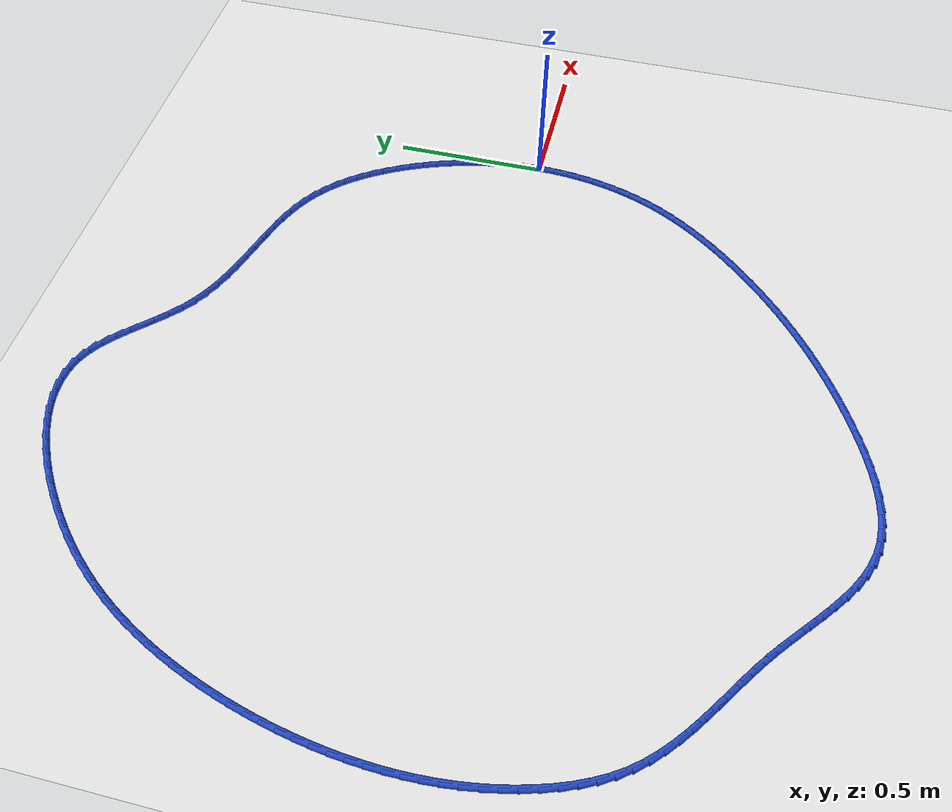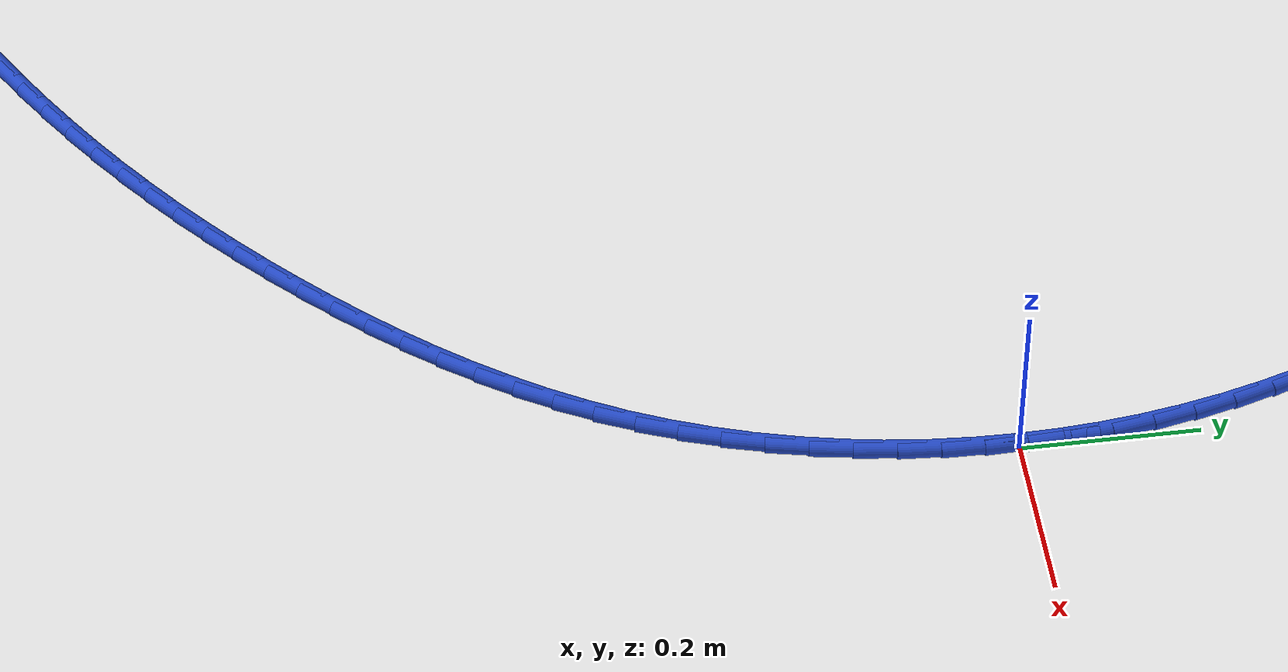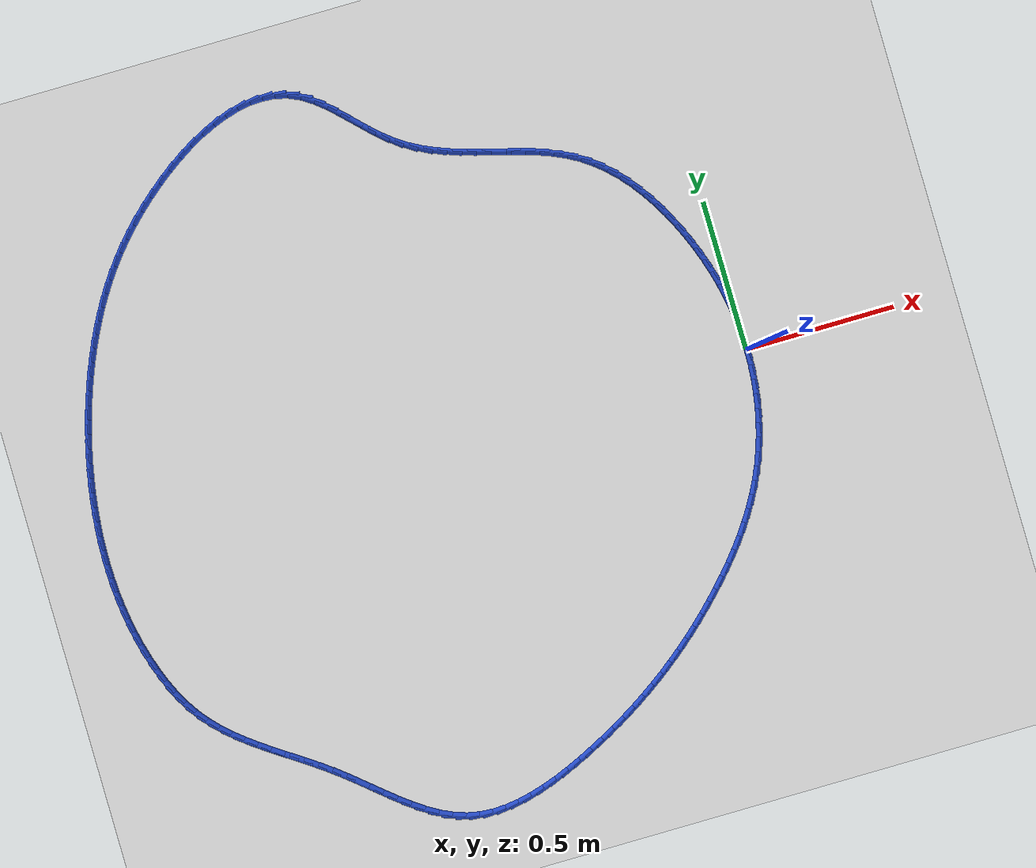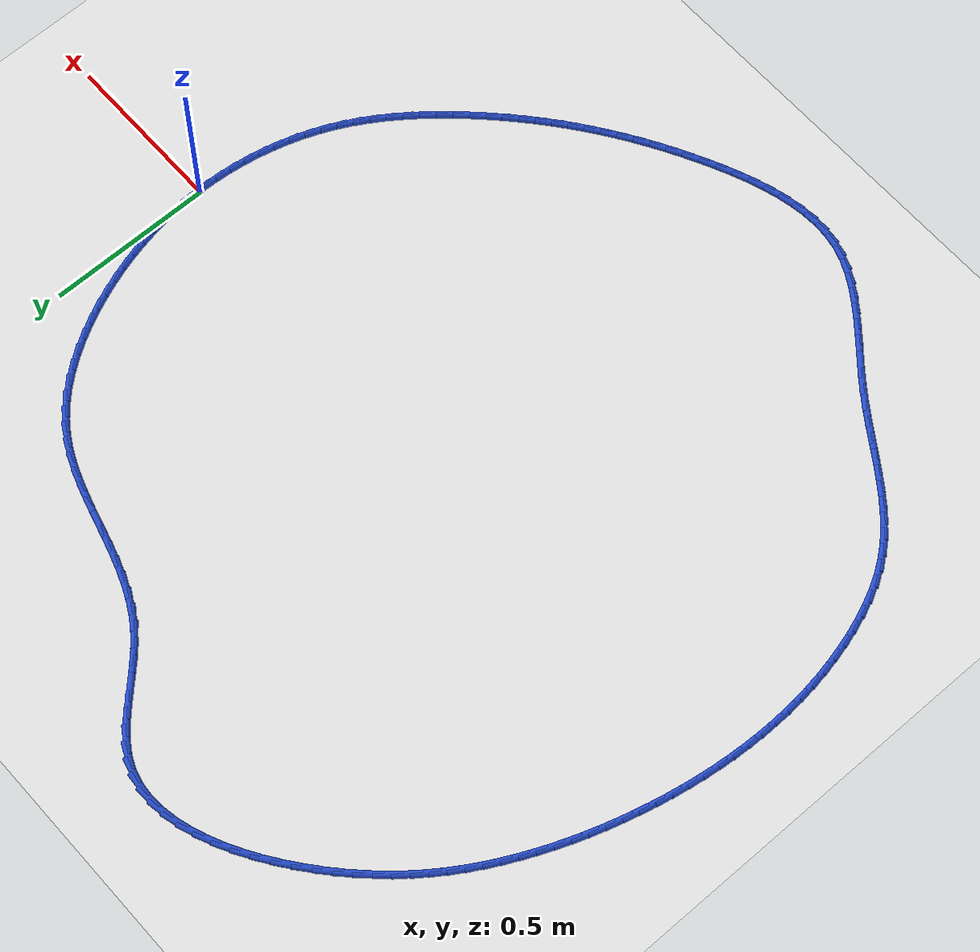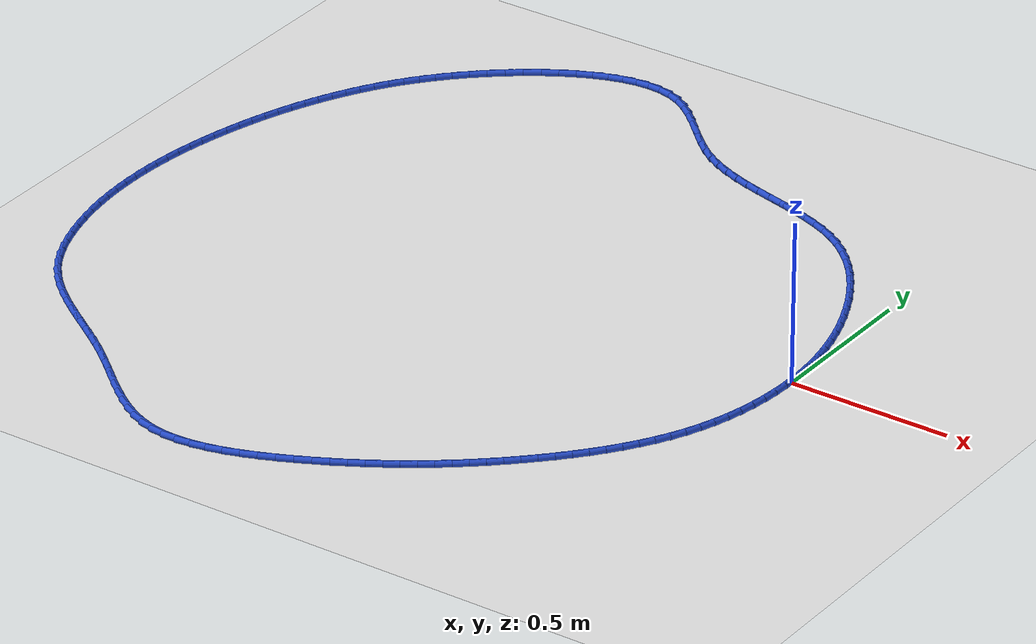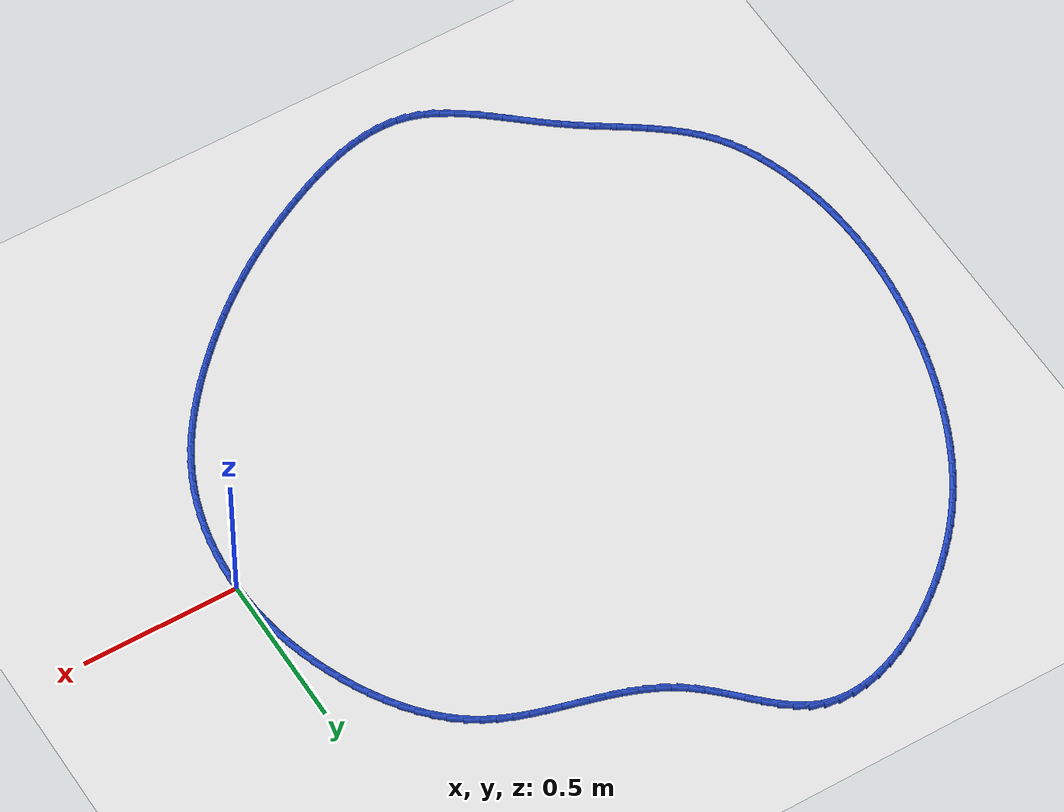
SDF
<sdf version="1.6">
 <world name="default">
  <light name="sun" type="directional">
   <pose>0 0 10 0 -0 0</pose>
   <diffuse>0.8 0.8 0.8 1</diffuse>
   <specular>0.2 0.2 0.2 1</specular>
   <attenuation>
    <range>1000</range>
    <constant>0.9</constant>
    <linear>0.01</linear>
    <quadratic>0.001</quadratic>
   </attenuation>
   <direction>-0.5 0.1 -0.9</direction>
  </light>
  <model name="ground_plane">
   <static>1</static>
   <link name="link">
    <collision name="collision">
     <geometry><plane><normal>0 0 1</normal><size>100 100</size></plane></geometry>
     <surface><friction><ode><mu>100</mu><mu2>50</mu2></ode></friction></surface>
    </collision>
    <visual name="visual">
     <cast_shadows>0</cast_shadows>
     <geometry><plane><normal>0 0 1</normal><size>100 100</size></plane></geometry>
     <material>
      <script><uri>file://media/materials/scripts/gazebo.material</uri><name>Gazebo/WhiteGlow</name></script>
     </material>
    </visual>
   </link>
  </model>
  <gravity>0 0 -9.8</gravity>
  <magnetic_field>6e-06 2.3e-05 -4.2e-05</magnetic_field>
  <atmosphere type="adiabatic"/>
  <physics name="default_physics" default="0" type="ode">
   <max_step_size>0.001</max_step_size>
   <real_time_factor>1</real_time_factor>
   <real_time_update_rate>1000</real_time_update_rate>
  </physics>
  <scene><ambient>0.4 0.4 0.4 1</ambient><background>0.7 0.7 0.7 1</background><shadows>1</shadows></scene>
  <spherical_coordinates>
   <surface_model>EARTH_WGS84</surface_model>
   <latitude_deg>0</latitude_deg>
   <longitude_deg>0</longitude_deg>
   <elevation>0</elevation>
   <heading_deg>0</heading_deg>
  </spherical_coordinates>
  <model name="line">
   <link name="link_0">
    <pose>-5.204170427930421e-17 -6.938893903907228e-17 0.01 0 1.57 -1.5430489320379732</pose>
    <collision name="collision">
     <geometry><cylinder><radius>0.01</radius><length>0.08</length></cylinder></geometry>
    </collision>
    <visual name="visual">
     <material>
      <script><name>Gazebo/Blue</name><uri>file://media/materials/scripts/gazebo.material</uri></script>
     </material>
     <geometry><cylinder><radius>0.01</radius><length>0.08</length></cylinder></geometry>
    </visual>
   </link>
   <link name="link_1">
    <pose>-0.0013068771516833977 0.04708700582048867 0.01 0 1.57 -1.4960087376007403</pose>
    <collision name="collision">
     <geometry><cylinder><radius>0.01</radius><length>0.08</length></cylinder></geometry>
    </collision>
    <visual name="visual">
     <material>
      <script><name>Gazebo/Blue</name><uri>file://media/materials/scripts/gazebo.material</uri></script>
     </material>
     <geometry><cylinder><radius>0.01</radius><length>0.08</length></cylinder></geometry>
    </visual>
   </link>
   <link name="link_2">
    <pose>-0.004819218803552588 0.09396364479403337 0.01 0 1.57 -1.449206003572129</pose>
    <collision name="collision">
     <geometry><cylinder><radius>0.01</radius><length>0.08</length></cylinder></geometry>
    </collision>
    <visual name="visual">
     <material>
      <script><name>Gazebo/Blue</name><uri>file://media/materials/scripts/gazebo.material</uri></script>
     </material>
     <geometry><cylinder><radius>0.01</radius><length>0.08</length></cylinder></geometry>
    </visual>
   </link>
   <link name="link_3">
    <pose>-0.010518211959583839 0.1406028859339611 0.01 0 1.57 -1.4027600925176416</pose>
    <collision name="collision">
     <geometry><cylinder><radius>0.01</radius><length>0.08</length></cylinder></geometry>
    </collision>
    <visual name="visual">
     <material>
      <script><name>Gazebo/Blue</name><uri>file://media/materials/scripts/gazebo.material</uri></script>
     </material>
     <geometry><cylinder><radius>0.01</radius><length>0.08</length></cylinder></geometry>
    </visual>
   </link>
   <link name="link_4">
    <pose>-0.01838504362375337 0.1869776982535991 0.01 0 1.57 -1.3567825330309908</pose>
    <collision name="collision">
     <geometry><cylinder><radius>0.01</radius><length>0.08</length></cylinder></geometry>
    </collision>
    <visual name="visual">
     <material>
      <script><name>Gazebo/Blue</name><uri>file://media/materials/scripts/gazebo.material</uri></script>
     </material>
     <geometry><cylinder><radius>0.01</radius><length>0.08</length></cylinder></geometry>
    </visual>
   </link>
   <link name="link_5">
    <pose>-0.02840090080003741 0.23306105076627465 0.01 0 1.57 -1.3113753411764149</pose>
    <collision name="collision">
     <geometry><cylinder><radius>0.01</radius><length>0.08</length></cylinder></geometry>
    </collision>
    <visual name="visual">
     <material>
      <script><name>Gazebo/Blue</name><uri>file://media/materials/scripts/gazebo.material</uri></script>
     </material>
     <geometry><cylinder><radius>0.01</radius><length>0.08</length></cylinder></geometry>
    </visual>
   </link>
   <link name="link_6">
    <pose>-0.040546970492412196 0.2788259124853148 0.01 0 1.57 -1.2666297400415574</pose>
    <collision name="collision">
     <geometry><cylinder><radius>0.01</radius><length>0.08</length></cylinder></geometry>
    </collision>
    <visual name="visual">
     <material>
      <script><name>Gazebo/Blue</name><uri>file://media/materials/scripts/gazebo.material</uri></script>
     </material>
     <geometry><cylinder><radius>0.01</radius><length>0.08</length></cylinder></geometry>
    </visual>
   </link>
   <link name="link_7">
    <pose>-0.054804439704853915 0.32424525242404667 0.01 0 1.57 -1.222625299350305</pose>
    <collision name="collision">
     <geometry><cylinder><radius>0.01</radius><length>0.08</length></cylinder></geometry>
    </collision>
    <visual name="visual">
     <material>
      <script><name>Gazebo/Blue</name><uri>file://media/materials/scripts/gazebo.material</uri></script>
     </material>
     <geometry><cylinder><radius>0.01</radius><length>0.08</length></cylinder></geometry>
    </visual>
   </link>
   <link name="link_8">
    <pose>-0.07115449544133881 0.36929203959579743 0.01 0 1.57 -1.1794268413409892</pose>
    <collision name="collision">
     <geometry><cylinder><radius>0.01</radius><length>0.08</length></cylinder></geometry>
    </collision>
    <visual name="visual">
     <material>
      <script><name>Gazebo/Blue</name><uri>file://media/materials/scripts/gazebo.material</uri></script>
     </material>
     <geometry><cylinder><radius>0.01</radius><length>0.08</length></cylinder></geometry>
    </visual>
   </link>
   <link name="link_9">
    <pose>-0.08957835645515856 0.41393898465846235 0.01 0 1.57 -1.1360576168852599</pose>
    <collision name="collision">
     <geometry><cylinder><radius>0.01</radius><length>0.08</length></cylinder></geometry>
    </collision>
    <visual name="visual">
     <material>
      <script><name>Gazebo/Blue</name><uri>file://media/materials/scripts/gazebo.material</uri></script>
     </material>
     <geometry><cylinder><radius>0.01</radius><length>0.08</length></cylinder></geometry>
    </visual>
   </link>
   <link name="link_10">
    <pose>-0.1100688396619832 0.458064419912318 0.01 0 1.57 -1.0896423183852832</pose>
    <collision name="collision">
     <geometry><cylinder><radius>0.01</radius><length>0.08</length></cylinder></geometry>
    </collision>
    <visual name="visual">
     <material>
      <script><name>Gazebo/Blue</name><uri>file://media/materials/scripts/gazebo.material</uri></script>
     </material>
     <geometry><cylinder><radius>0.01</radius><length>0.08</length></cylinder></geometry>
    </visual>
   </link>
   <link name="link_11">
    <pose>-0.13264757683827966 0.5013122009234536 0.01 0 1.57 -1.0390727693667015</pose>
    <collision name="collision">
     <geometry><cylinder><radius>0.01</radius><length>0.08</length></cylinder></geometry>
    </collision>
    <visual name="visual">
     <material>
      <script><name>Gazebo/Blue</name><uri>file://media/materials/scripts/gazebo.material</uri></script>
     </material>
     <geometry><cylinder><radius>0.01</radius><length>0.08</length></cylinder></geometry>
    </visual>
   </link>
   <link name="link_12">
    <pose>-0.15734059874754985 0.5432903871414707 0.01 0 1.57 -0.9835570497863425</pose>
    <collision name="collision">
     <geometry><cylinder><radius>0.01</radius><length>0.08</length></cylinder></geometry>
    </collision>
    <visual name="visual">
     <material>
      <script><name>Gazebo/Blue</name><uri>file://media/materials/scripts/gazebo.material</uri></script>
     </material>
     <geometry><cylinder><radius>0.01</radius><length>0.08</length></cylinder></geometry>
    </visual>
   </link>
   <link name="link_13">
    <pose>-0.18417393615329578 0.5836070380159706 0.01 0 1.57 -0.922257972953148</pose>
    <collision name="collision">
     <geometry><cylinder><radius>0.01</radius><length>0.08</length></cylinder></geometry>
    </collision>
    <visual name="visual">
     <material>
      <script><name>Gazebo/Blue</name><uri>file://media/materials/scripts/gazebo.material</uri></script>
     </material>
     <geometry><cylinder><radius>0.01</radius><length>0.08</length></cylinder></geometry>
    </visual>
   </link>
   <link name="link_14">
    <pose>-0.2131736198190191 0.6218702129965543 0.01 0 1.57 -0.8543189788384198</pose>
    <collision name="collision">
     <geometry><cylinder><radius>0.01</radius><length>0.08</length></cylinder></geometry>
    </collision>
    <visual name="visual">
     <material>
      <script><name>Gazebo/Blue</name><uri>file://media/materials/scripts/gazebo.material</uri></script>
     </material>
     <geometry><cylinder><radius>0.01</radius><length>0.08</length></cylinder></geometry>
    </visual>
   </link>
   <link name="link_15">
    <pose>-0.24436568050822194 0.6576879715328234 0.01 0 1.57 -0.7789204516399986</pose>
    <collision name="collision">
     <geometry><cylinder><radius>0.01</radius><length>0.08</length></cylinder></geometry>
    </collision>
    <visual name="visual">
     <material>
      <script><name>Gazebo/Blue</name><uri>file://media/materials/scripts/gazebo.material</uri></script>
     </material>
     <geometry><cylinder><radius>0.01</radius><length>0.08</length></cylinder></geometry>
    </visual>
   </link>
   <link name="link_16">
    <pose>-0.277776148984406 0.6906683730743791 0.01 0 1.57 -0.6953781946876039</pose>
    <collision name="collision">
     <geometry><cylinder><radius>0.01</radius><length>0.08</length></cylinder></geometry>
    </collision>
    <visual name="visual">
     <material>
      <script><name>Gazebo/Blue</name><uri>file://media/materials/scripts/gazebo.material</uri></script>
     </material>
     <geometry><cylinder><radius>0.01</radius><length>0.08</length></cylinder></geometry>
    </visual>
   </link>
   <link name="link_17">
    <pose>-0.3134310560110734 0.720419477070823 0.01 0 1.57 -0.603292855712652</pose>
    <collision name="collision">
     <geometry><cylinder><radius>0.01</radius><length>0.08</length></cylinder></geometry>
    </collision>
    <visual name="visual">
     <material>
      <script><name>Gazebo/Blue</name><uri>file://media/materials/scripts/gazebo.material</uri></script>
     </material>
     <geometry><cylinder><radius>0.01</radius><length>0.08</length></cylinder></geometry>
    </visual>
   </link>
   <link name="link_18">
    <pose>-0.351356424230301 0.7465493653353416 0.01 0 1.57 -0.5074278709803657</pose>
    <collision name="collision">
     <geometry><cylinder><radius>0.01</radius><length>0.08</length></cylinder></geometry>
    </collision>
    <visual name="visual">
     <material>
      <script><name>Gazebo/Blue</name><uri>file://media/materials/scripts/gazebo.material</uri></script>
     </material>
     <geometry><cylinder><radius>0.01</radius><length>0.08</length></cylinder></geometry>
    </visual>
   </link>
   <link name="link_19">
    <pose>-0.3915039302045219 0.7688708429847803 0.01 0 1.57 -0.4248515451725392</pose>
    <collision name="collision">
     <geometry><cylinder><radius>0.01</radius><length>0.08</length></cylinder></geometry>
    </collision>
    <visual name="visual">
     <material>
      <script><name>Gazebo/Blue</name><uri>file://media/materials/scripts/gazebo.material</uri></script>
     </material>
     <geometry><cylinder><radius>0.01</radius><length>0.08</length></cylinder></geometry>
    </visual>
   </link>
   <link name="link_20">
    <pose>-0.4335693364193069 0.7879014136960005 0.01 0 1.57 -0.3597683688413712</pose>
    <collision name="collision">
     <geometry><cylinder><radius>0.01</radius><length>0.08</length></cylinder></geometry>
    </collision>
    <visual name="visual">
     <material>
      <script><name>Gazebo/Blue</name><uri>file://media/materials/scripts/gazebo.material</uri></script>
     </material>
     <geometry><cylinder><radius>0.01</radius><length>0.08</length></cylinder></geometry>
    </visual>
   </link>
   <link name="link_21">
    <pose>-0.4771933829070298 0.8043100938879991 0.01 0 1.57 -0.3119741467545271</pose>
    <collision name="collision">
     <geometry><cylinder><radius>0.01</radius><length>0.08</length></cylinder></geometry>
    </collision>
    <visual name="visual">
     <material>
      <script><name>Gazebo/Blue</name><uri>file://media/materials/scripts/gazebo.material</uri></script>
     </material>
     <geometry><cylinder><radius>0.01</radius><length>0.08</length></cylinder></geometry>
    </visual>
   </link>
   <link name="link_22">
    <pose>-0.5220168097000639 0.8187658999797733 0.01 0 1.57 -0.2808331020607207</pose>
    <collision name="collision">
     <geometry><cylinder><radius>0.01</radius><length>0.08</length></cylinder></geometry>
    </collision>
    <visual name="visual">
     <material>
      <script><name>Gazebo/Blue</name><uri>file://media/materials/scripts/gazebo.material</uri></script>
     </material>
     <geometry><cylinder><radius>0.01</radius><length>0.08</length></cylinder></geometry>
    </visual>
   </link>
   <link name="link_23">
    <pose>-0.5676803568307829 0.8319378483903199 0.01 0 1.57 -0.2656926023756087</pose>
    <collision name="collision">
     <geometry><cylinder><radius>0.01</radius><length>0.08</length></cylinder></geometry>
    </collision>
    <visual name="visual">
     <material>
      <script><name>Gazebo/Blue</name><uri>file://media/materials/scripts/gazebo.material</uri></script>
     </material>
     <geometry><cylinder><radius>0.01</radius><length>0.08</length></cylinder></geometry>
    </visual>
   </link>
   <link name="link_24">
    <pose>-0.6138247643315603 0.844494955538636 0.01 0 1.57 -0.2661168557164873</pose>
    <collision name="collision">
     <geometry><cylinder><radius>0.01</radius><length>0.08</length></cylinder></geometry>
    </collision>
    <visual name="visual">
     <material>
      <script><name>Gazebo/Blue</name><uri>file://media/materials/scripts/gazebo.material</uri></script>
     </material>
     <geometry><cylinder><radius>0.01</radius><length>0.08</length></cylinder></geometry>
    </visual>
   </link>
   <link name="link_25">
    <pose>-0.66009077223477 0.8571062378437185 0.01 0 1.57 -0.28198190255938627</pose>
    <collision name="collision">
     <geometry><cylinder><radius>0.01</radius><length>0.08</length></cylinder></geometry>
    </collision>
    <visual name="visual">
     <material>
      <script><name>Gazebo/Blue</name><uri>file://media/materials/scripts/gazebo.material</uri></script>
     </material>
     <geometry><cylinder><radius>0.01</radius><length>0.08</length></cylinder></geometry>
    </visual>
   </link>
   <link name="link_26">
    <pose>-0.7061191205727851 0.8704407117245646 0.01 0 1.57 -0.31346458885444073</pose>
    <collision name="collision">
     <geometry><cylinder><radius>0.01</radius><length>0.08</length></cylinder></geometry>
    </collision>
    <visual name="visual">
     <material>
      <script><name>Gazebo/Blue</name><uri>file://media/materials/scripts/gazebo.material</uri></script>
     </material>
     <geometry><cylinder><radius>0.01</radius><length>0.08</length></cylinder></geometry>
    </visual>
   </link>
   <link name="link_27">
    <pose>-0.7515505493779797 0.8851673936001715 0.01 0 1.57 -0.3609311210586704</pose>
    <collision name="collision">
     <geometry><cylinder><radius>0.01</radius><length>0.08</length></cylinder></geometry>
    </collision>
    <visual name="visual">
     <material>
      <script><name>Gazebo/Blue</name><uri>file://media/materials/scripts/gazebo.material</uri></script>
     </material>
     <geometry><cylinder><radius>0.01</radius><length>0.08</length></cylinder></geometry>
    </visual>
   </link>
   <link name="link_28">
    <pose>-0.7960257986827268 0.9019552998895357 0.01 0 1.57 -0.42470658442955783</pose>
    <collision name="collision">
     <geometry><cylinder><radius>0.01</radius><length>0.08</length></cylinder></geometry>
    </collision>
    <visual name="visual">
     <material>
      <script><name>Gazebo/Blue</name><uri>file://media/materials/scripts/gazebo.material</uri></script>
     </material>
     <geometry><cylinder><radius>0.01</radius><length>0.08</length></cylinder></geometry>
    </visual>
   </link>
   <link name="link_29">
    <pose>-0.8391856085194009 0.9214734470116548 0.01 0 1.57 -0.5047029655454061</pose>
    <collision name="collision">
     <geometry><cylinder><radius>0.01</radius><length>0.08</length></cylinder></geometry>
    </collision>
    <visual name="visual">
     <material>
      <script><name>Gazebo/Blue</name><uri>file://media/materials/scripts/gazebo.material</uri></script>
     </material>
     <geometry><cylinder><radius>0.01</radius><length>0.08</length></cylinder></geometry>
    </visual>
   </link>
   <link name="link_30">
    <pose>-0.8806707189203746 0.9443908513855255 0.01 0 1.57 -0.5998304162295812</pose>
    <collision name="collision">
     <geometry><cylinder><radius>0.01</radius><length>0.08</length></cylinder></geometry>
    </collision>
    <visual name="visual">
     <material>
      <script><name>Gazebo/Blue</name><uri>file://media/materials/scripts/gazebo.material</uri></script>
     </material>
     <geometry><cylinder><radius>0.01</radius><length>0.08</length></cylinder></geometry>
    </visual>
   </link>
   <link name="link_31">
    <pose>-0.9201237133830552 0.9713722761646811 0.01 0 1.57 -0.6934824765537155</pose>
    <collision name="collision">
     <geometry><cylinder><radius>0.01</radius><length>0.08</length></cylinder></geometry>
    </collision>
    <visual name="visual">
     <material>
      <script><name>Gazebo/Blue</name><uri>file://media/materials/scripts/gazebo.material</uri></script>
     </material>
     <geometry><cylinder><radius>0.01</radius><length>0.08</length></cylinder></geometry>
    </visual>
   </link>
   <link name="link_32">
    <pose>-0.9574748278691393 1.0024188091575708 0.01 0 1.57 -0.7560283244380805</pose>
    <collision name="collision">
     <geometry><cylinder><radius>0.01</radius><length>0.08</length></cylinder></geometry>
    </collision>
    <visual name="visual">
     <material>
      <script><name>Gazebo/Blue</name><uri>file://media/materials/scripts/gazebo.material</uri></script>
     </material>
     <geometry><cylinder><radius>0.01</radius><length>0.08</length></cylinder></geometry>
    </visual>
   </link>
   <link name="link_33">
    <pose>-0.9932515942823049 1.036153449542708 0.01 0 1.57 -0.7864017336866168</pose>
    <collision name="collision">
     <geometry><cylinder><radius>0.01</radius><length>0.08</length></cylinder></geometry>
    </collision>
    <visual name="visual">
     <material>
      <script><name>Gazebo/Blue</name><uri>file://media/materials/scripts/gazebo.material</uri></script>
     </material>
     <geometry><cylinder><radius>0.01</radius><length>0.08</length></cylinder></geometry>
    </visual>
   </link>
   <link name="link_34">
    <pose>-1.028055887921355 1.0710276704922685 0.01 0 1.57 -0.7858564941942627</pose>
    <collision name="collision">
     <geometry><cylinder><radius>0.01</radius><length>0.08</length></cylinder></geometry>
    </collision>
    <visual name="visual">
     <material>
      <script><name>Gazebo/Blue</name><uri>file://media/materials/scripts/gazebo.material</uri></script>
     </material>
     <geometry><cylinder><radius>0.01</radius><length>0.08</length></cylinder></geometry>
    </visual>
   </link>
   <link name="link_35">
    <pose>-1.0624895840850905 1.1054929451784246 0.01 0 1.57 -0.7532954064187378</pose>
    <collision name="collision">
     <geometry><cylinder><radius>0.01</radius><length>0.08</length></cylinder></geometry>
    </collision>
    <visual name="visual">
     <material>
      <script><name>Gazebo/Blue</name><uri>file://media/materials/scripts/gazebo.material</uri></script>
     </material>
     <geometry><cylinder><radius>0.01</radius><length>0.08</length></cylinder></geometry>
    </visual>
   </link>
   <link name="link_36">
    <pose>-1.0971545580723139 1.1380007467733504 0.01 0 1.57 -0.6850183388531048</pose>
    <collision name="collision">
     <geometry><cylinder><radius>0.01</radius><length>0.08</length></cylinder></geometry>
    </collision>
    <visual name="visual">
     <material>
      <script><name>Gazebo/Blue</name><uri>file://media/materials/scripts/gazebo.material</uri></script>
     </material>
     <geometry><cylinder><radius>0.01</radius><length>0.08</length></cylinder></geometry>
    </visual>
   </link>
   <link name="link_37">
    <pose>-1.1326526851818268 1.16700254844922 0.01 0 1.57 -0.5752461272479498</pose>
    <collision name="collision">
     <geometry><cylinder><radius>0.01</radius><length>0.08</length></cylinder></geometry>
    </collision>
    <visual name="visual">
     <material>
      <script><name>Gazebo/Blue</name><uri>file://media/materials/scripts/gazebo.material</uri></script>
     </material>
     <geometry><cylinder><radius>0.01</radius><length>0.08</length></cylinder></geometry>
    </visual>
   </link>
   <link name="link_38">
    <pose>-1.1695858407124322 1.1909498233782077 0.01 0 1.57 -0.41943407301285196</pose>
    <collision name="collision">
     <geometry><cylinder><radius>0.01</radius><length>0.08</length></cylinder></geometry>
    </collision>
    <visual name="visual">
     <material>
      <script><name>Gazebo/Blue</name><uri>file://media/materials/scripts/gazebo.material</uri></script>
     </material>
     <geometry><cylinder><radius>0.01</radius><length>0.08</length></cylinder></geometry>
    </visual>
   </link>
   <link name="link_39">
    <pose>-1.2085433452273298 1.2083207381532461 0.01 0 1.57 -0.24233388045073406</pose>
    <collision name="collision">
     <geometry><cylinder><radius>0.01</radius><length>0.08</length></cylinder></geometry>
    </collision>
    <visual name="visual">
     <material>
      <script><name>Gazebo/Blue</name><uri>file://media/materials/scripts/gazebo.material</uri></script>
     </material>
     <geometry><cylinder><radius>0.01</radius><length>0.08</length></cylinder></geometry>
    </visual>
   </link>
   <link name="link_40">
    <pose>-1.2496917714463065 1.218492290407449 0.01 0 1.57 -0.0798975234013154</pose>
    <collision name="collision">
     <geometry><cylinder><radius>0.01</radius><length>0.08</length></cylinder></geometry>
    </collision>
    <visual name="visual">
     <material>
      <script><name>Gazebo/Blue</name><uri>file://media/materials/scripts/gazebo.material</uri></script>
     </material>
     <geometry><cylinder><radius>0.01</radius><length>0.08</length></cylinder></geometry>
    </visual>
   </link>
   <link name="link_41">
    <pose>-1.2926835831193815 1.2219345575075304 0.01 0 1.57 0.061800199550257416</pose>
    <collision name="collision">
     <geometry><cylinder><radius>0.01</radius><length>0.08</length></cylinder></geometry>
    </collision>
    <visual name="visual">
     <material>
      <script><name>Gazebo/Blue</name><uri>file://media/materials/scripts/gazebo.material</uri></script>
     </material>
     <geometry><cylinder><radius>0.01</radius><length>0.08</length></cylinder></geometry>
    </visual>
   </link>
   <link name="link_42">
    <pose>-1.3371401974760173 1.2191836267994383 0.01 0 1.57 0.18256268368402495</pose>
    <collision name="collision">
     <geometry><cylinder><radius>0.01</radius><length>0.08</length></cylinder></geometry>
    </collision>
    <visual name="visual">
     <material>
      <script><name>Gazebo/Blue</name><uri>file://media/materials/scripts/gazebo.material</uri></script>
     </material>
     <geometry><cylinder><radius>0.01</radius><length>0.08</length></cylinder></geometry>
    </visual>
   </link>
   <link name="link_43">
    <pose>-1.3826830317456784 1.2107755856291218 0.01 0 1.57 0.28457789872275924</pose>
    <collision name="collision">
     <geometry><cylinder><radius>0.01</radius><length>0.08</length></cylinder></geometry>
    </collision>
    <visual name="visual">
     <material>
      <script><name>Gazebo/Blue</name><uri>file://media/materials/scripts/gazebo.material</uri></script>
     </material>
     <geometry><cylinder><radius>0.01</radius><length>0.08</length></cylinder></geometry>
    </visual>
   </link>
   <link name="link_44">
    <pose>-1.4289335031578272 1.1972465213425292 0.01 0 1.57 0.370886440779815</pose>
    <collision name="collision">
     <geometry><cylinder><radius>0.01</radius><length>0.08</length></cylinder></geometry>
    </collision>
    <visual name="visual">
     <material>
      <script><name>Gazebo/Blue</name><uri>file://media/materials/scripts/gazebo.material</uri></script>
     </material>
     <geometry><cylinder><radius>0.01</radius><length>0.08</length></cylinder></geometry>
    </visual>
   </link>
   <link name="link_45">
    <pose>-1.4755130289419285 1.1791325212856092 0.01 0 1.57 0.44451918354778513</pose>
    <collision name="collision">
     <geometry><cylinder><radius>0.01</radius><length>0.08</length></cylinder></geometry>
    </collision>
    <visual name="visual">
     <material>
      <script><name>Gazebo/Blue</name><uri>file://media/materials/scripts/gazebo.material</uri></script>
     </material>
     <geometry><cylinder><radius>0.01</radius><length>0.08</length></cylinder></geometry>
    </visual>
   </link>
   <link name="link_46">
    <pose>-1.522043026327444 1.1569696728043097 0.01 0 1.57 0.5081495995070204</pose>
    <collision name="collision">
     <geometry><cylinder><radius>0.01</radius><length>0.08</length></cylinder></geometry>
    </collision>
    <visual name="visual">
     <material>
      <script><name>Gazebo/Blue</name><uri>file://media/materials/scripts/gazebo.material</uri></script>
     </material>
     <geometry><cylinder><radius>0.01</radius><length>0.08</length></cylinder></geometry>
    </visual>
   </link>
   <link name="link_47">
    <pose>-1.5681449125438383 1.1312940632445805 0.01 0 1.57 0.5640228785743613</pose>
    <collision name="collision">
     <geometry><cylinder><radius>0.01</radius><length>0.08</length></cylinder></geometry>
    </collision>
    <visual name="visual">
     <material>
      <script><name>Gazebo/Blue</name><uri>file://media/materials/scripts/gazebo.material</uri></script>
     </material>
     <geometry><cylinder><radius>0.01</radius><length>0.08</length></cylinder></geometry>
    </visual>
   </link>
   <link name="link_48">
    <pose>-1.613440104820574 1.1026417799523693 0.01 0 1.57 0.6140038126901969</pose>
    <collision name="collision">
     <geometry><cylinder><radius>0.01</radius><length>0.08</length></cylinder></geometry>
    </collision>
    <visual name="visual">
     <material>
      <script><name>Gazebo/Blue</name><uri>file://media/materials/scripts/gazebo.material</uri></script>
     </material>
     <geometry><cylinder><radius>0.01</radius><length>0.08</length></cylinder></geometry>
    </visual>
   </link>
   <link name="link_49">
    <pose>-1.6575500203871159 1.0715489102736246 0.01 0 1.57 0.6596649655837512</pose>
    <collision name="collision">
     <geometry><cylinder><radius>0.01</radius><length>0.08</length></cylinder></geometry>
    </collision>
    <visual name="visual">
     <material>
      <script><name>Gazebo/Blue</name><uri>file://media/materials/scripts/gazebo.material</uri></script>
     </material>
     <geometry><cylinder><radius>0.01</radius><length>0.08</length></cylinder></geometry>
    </visual>
   </link>
   <link name="link_50">
    <pose>-1.7000960764729265 1.0385515415542952 0.01 0 1.57 0.7023843152716511</pose>
    <collision name="collision">
     <geometry><cylinder><radius>0.01</radius><length>0.08</length></cylinder></geometry>
    </collision>
    <visual name="visual">
     <material>
      <script><name>Gazebo/Blue</name><uri>file://media/materials/scripts/gazebo.material</uri></script>
     </material>
     <geometry><cylinder><radius>0.01</radius><length>0.08</length></cylinder></geometry>
    </visual>
   </link>
   <link name="link_51">
    <pose>-1.740699690307469 1.0041857611403295 0.01 0 1.57 0.7434476590716523</pose>
    <collision name="collision">
     <geometry><cylinder><radius>0.01</radius><length>0.08</length></cylinder></geometry>
    </collision>
    <visual name="visual">
     <material>
      <script><name>Gazebo/Blue</name><uri>file://media/materials/scripts/gazebo.material</uri></script>
     </material>
     <geometry><cylinder><radius>0.01</radius><length>0.08</length></cylinder></geometry>
    </visual>
   </link>
   <link name="link_52">
    <pose>-1.7789829456355228 0.9689869261398266 0.01 0 1.57 0.7843617866977304</pose>
    <collision name="collision">
     <geometry><cylinder><radius>0.01</radius><length>0.08</length></cylinder></geometry>
    </collision>
    <visual name="visual">
     <material>
      <script><name>Gazebo/Blue</name><uri>file://media/materials/scripts/gazebo.material</uri></script>
     </material>
     <geometry><cylinder><radius>0.01</radius><length>0.08</length></cylinder></geometry>
    </visual>
   </link>
   <link name="link_53">
    <pose>-1.8147190945266025 0.9333247728120583 0.01 0 1.57 0.8260778291966491</pose>
    <collision name="collision">
     <geometry><cylinder><radius>0.01</radius><length>0.08</length></cylinder></geometry>
    </collision>
    <visual name="visual">
     <material>
      <script><name>Gazebo/Blue</name><uri>file://media/materials/scripts/gazebo.material</uri></script>
     </material>
     <geometry><cylinder><radius>0.01</radius><length>0.08</length></cylinder></geometry>
    </visual>
   </link>
   <link name="link_54">
    <pose>-1.8480236449829905 0.8971940599320922 0.01 0 1.57 0.8682398692474244</pose>
    <collision name="collision">
     <geometry><cylinder><radius>0.01</radius><length>0.08</length></cylinder></geometry>
    </collision>
    <visual name="visual">
     <material>
      <script><name>Gazebo/Blue</name><uri>file://media/materials/scripts/gazebo.material</uri></script>
     </material>
     <geometry><cylinder><radius>0.01</radius><length>0.08</length></cylinder></geometry>
    </visual>
   </link>
   <link name="link_55">
    <pose>-1.879059196159233 0.8605379529493156 0.01 0 1.57 0.9103222837495785</pose>
    <collision name="collision">
     <geometry><cylinder><radius>0.01</radius><length>0.08</length></cylinder></geometry>
    </collision>
    <visual name="visual">
     <material>
      <script><name>Gazebo/Blue</name><uri>file://media/materials/scripts/gazebo.material</uri></script>
     </material>
     <geometry><cylinder><radius>0.01</radius><length>0.08</length></cylinder></geometry>
    </visual>
   </link>
   <link name="link_56">
    <pose>-1.9079883472098769 0.8232996173131154 0.01 0 1.57 0.9517704896321063</pose>
    <collision name="collision">
     <geometry><cylinder><radius>0.01</radius><length>0.08</length></cylinder></geometry>
    </collision>
    <visual name="visual">
     <material>
      <script><name>Gazebo/Blue</name><uri>file://media/materials/scripts/gazebo.material</uri></script>
     </material>
     <geometry><cylinder><radius>0.01</radius><length>0.08</length></cylinder></geometry>
    </visual>
   </link>
   <link name="link_57">
    <pose>-1.9349736972894702 0.7854222184728795 0.01 0 1.57 0.9920281874642862</pose>
    <collision name="collision">
     <geometry><cylinder><radius>0.01</radius><length>0.08</length></cylinder></geometry>
    </collision>
    <visual name="visual">
     <material>
      <script><name>Gazebo/Blue</name><uri>file://media/materials/scripts/gazebo.material</uri></script>
     </material>
     <geometry><cylinder><radius>0.01</radius><length>0.08</length></cylinder></geometry>
    </visual>
   </link>
   <link name="link_58">
    <pose>-1.9601778455525602 0.7468489218779945 0.01 0 1.57 1.0305651630379213</pose>
    <collision name="collision">
     <geometry><cylinder><radius>0.01</radius><length>0.08</length></cylinder></geometry>
    </collision>
    <visual name="visual">
     <material>
      <script><name>Gazebo/Blue</name><uri>file://media/materials/scripts/gazebo.material</uri></script>
     </material>
     <geometry><cylinder><radius>0.01</radius><length>0.08</length></cylinder></geometry>
    </visual>
   </link>
   <link name="link_59">
    <pose>-1.9837633911536936 0.7075228929778484 0.01 0 1.57 1.0669023086766773</pose>
    <collision name="collision">
     <geometry><cylinder><radius>0.01</radius><length>0.08</length></cylinder></geometry>
    </collision>
    <visual name="visual">
     <material>
      <script><name>Gazebo/Blue</name><uri>file://media/materials/scripts/gazebo.material</uri></script>
     </material>
     <geometry><cylinder><radius>0.01</radius><length>0.08</length></cylinder></geometry>
    </visual>
   </link>
   <link name="link_60">
    <pose>-2.0058929332474182 0.6673872972218282 0.01 0 1.57 1.1006311374016686</pose>
    <collision name="collision">
     <geometry><cylinder><radius>0.01</radius><length>0.08</length></cylinder></geometry>
    </collision>
    <visual name="visual">
     <material>
      <script><name>Gazebo/Blue</name><uri>file://media/materials/scripts/gazebo.material</uri></script>
     </material>
     <geometry><cylinder><radius>0.01</radius><length>0.08</length></cylinder></geometry>
    </visual>
   </link>
   <link name="link_61">
    <pose>-2.026729070988281 0.6263853000593211 0.01 0 1.57 1.1317554121376976</pose>
    <collision name="collision">
     <geometry><cylinder><radius>0.01</radius><length>0.08</length></cylinder></geometry>
    </collision>
    <visual name="visual">
     <material>
      <script><name>Gazebo/Blue</name><uri>file://media/materials/scripts/gazebo.material</uri></script>
     </material>
     <geometry><cylinder><radius>0.01</radius><length>0.08</length></cylinder></geometry>
    </visual>
   </link>
   <link name="link_62">
    <pose>-2.046407718862001 0.5844810117295631 0.01 0 1.57 1.161544671396139</pose>
    <collision name="collision">
     <geometry><cylinder><radius>0.01</radius><length>0.08</length></cylinder></geometry>
    </collision>
    <visual name="visual">
     <material>
      <script><name>Gazebo/Blue</name><uri>file://media/materials/scripts/gazebo.material</uri></script>
     </material>
     <geometry><cylinder><radius>0.01</radius><length>0.08</length></cylinder></geometry>
    </visual>
   </link>
   <link name="link_63">
    <pose>-2.0649518313613777 0.5417272047418132 0.01 0 1.57 1.1904522034044929</pose>
    <collision name="collision">
     <geometry><cylinder><radius>0.01</radius><length>0.08</length></cylinder></geometry>
    </collision>
    <visual name="visual">
     <material>
      <script><name>Gazebo/Blue</name><uri>file://media/materials/scripts/gazebo.material</uri></script>
     </material>
     <geometry><cylinder><radius>0.01</radius><length>0.08</length></cylinder></geometry>
    </visual>
   </link>
   <link name="link_64">
    <pose>-2.0823544780579373 0.4982001082725154 0.01 0 1.57 1.2185798499001455</pose>
    <collision name="collision">
     <geometry><cylinder><radius>0.01</radius><length>0.08</length></cylinder></geometry>
    </collision>
    <visual name="visual">
     <material>
      <script><name>Gazebo/Blue</name><uri>file://media/materials/scripts/gazebo.material</uri></script>
     </material>
     <geometry><cylinder><radius>0.01</radius><length>0.08</length></cylinder></geometry>
    </visual>
   </link>
   <link name="link_65">
    <pose>-2.0986087283330734 0.4539759516473518 0.01 0 1.57 1.246026530631225</pose>
    <collision name="collision">
     <geometry><cylinder><radius>0.01</radius><length>0.08</length></cylinder></geometry>
    </collision>
    <visual name="visual">
     <material>
      <script><name>Gazebo/Blue</name><uri>file://media/materials/scripts/gazebo.material</uri></script>
     </material>
     <geometry><cylinder><radius>0.01</radius><length>0.08</length></cylinder></geometry>
    </visual>
   </link>
   <link name="link_66">
    <pose>-2.1137076515681756 0.4091309641920046 0.01 0 1.57 1.2728884398216824</pose>
    <collision name="collision">
     <geometry><cylinder><radius>0.01</radius><length>0.08</length></cylinder></geometry>
    </collision>
    <visual name="visual">
     <material>
      <script><name>Gazebo/Blue</name><uri>file://media/materials/scripts/gazebo.material</uri></script>
     </material>
     <geometry><cylinder><radius>0.01</radius><length>0.08</length></cylinder></geometry>
    </visual>
   </link>
   <link name="link_67">
    <pose>-2.1276443171446364 0.3637413752321555 0.01 0 1.57 1.2992593527315281</pose>
    <collision name="collision">
     <geometry><cylinder><radius>0.01</radius><length>0.08</length></cylinder></geometry>
    </collision>
    <visual name="visual">
     <material>
      <script><name>Gazebo/Blue</name><uri>file://media/materials/scripts/gazebo.material</uri></script>
     </material>
     <geometry><cylinder><radius>0.01</radius><length>0.08</length></cylinder></geometry>
    </visual>
   </link>
   <link name="link_68">
    <pose>-2.140411794443847 0.31788341409348747 0.01 0 1.57 1.3252310185312075</pose>
    <collision name="collision">
     <geometry><cylinder><radius>0.01</radius><length>0.08</length></cylinder></geometry>
    </collision>
    <visual name="visual">
     <material>
      <script><name>Gazebo/Blue</name><uri>file://media/materials/scripts/gazebo.material</uri></script>
     </material>
     <geometry><cylinder><radius>0.01</radius><length>0.08</length></cylinder></geometry>
    </visual>
   </link>
   <link name="link_69">
    <pose>-2.1520031528471995 0.27163331010168223 0.01 0 1.57 1.3509429113099136</pose>
    <collision name="collision">
     <geometry><cylinder><radius>0.01</radius><length>0.08</length></cylinder></geometry>
    </collision>
    <visual name="visual">
     <material>
      <script><name>Gazebo/Blue</name><uri>file://media/materials/scripts/gazebo.material</uri></script>
     </material>
     <geometry><cylinder><radius>0.01</radius><length>0.08</length></cylinder></geometry>
    </visual>
   </link>
   <link name="link_70">
    <pose>-2.1624093125047112 0.22506612591006184 0.01 0 1.57 1.3771962187396718</pose>
    <collision name="collision">
     <geometry><cylinder><radius>0.01</radius><length>0.08</length></cylinder></geometry>
    </collision>
    <visual name="visual">
     <material>
      <script><name>Gazebo/Blue</name><uri>file://media/materials/scripts/gazebo.material</uri></script>
     </material>
     <geometry><cylinder><radius>0.01</radius><length>0.08</length></cylinder></geometry>
    </visual>
   </link>
   <link name="link_71">
    <pose>-2.1715898584196007 0.17823991443994347 0.01 0 1.57 1.4045970773944596</pose>
    <collision name="collision">
     <geometry><cylinder><radius>0.01</radius><length>0.08</length></cylinder></geometry>
    </collision>
    <visual name="visual">
     <material>
      <script><name>Gazebo/Blue</name><uri>file://media/materials/scripts/gazebo.material</uri></script>
     </material>
     <geometry><cylinder><radius>0.01</radius><length>0.08</length></cylinder></geometry>
    </visual>
   </link>
   <link name="link_72">
    <pose>-2.1794806682070234 0.1311998594749961 0.01 0 1.57 1.4332152109165468</pose>
    <collision name="collision">
     <geometry><cylinder><radius>0.01</radius><length>0.08</length></cylinder></geometry>
    </collision>
    <visual name="visual">
     <material>
      <script><name>Gazebo/Blue</name><uri>file://media/materials/scripts/gazebo.material</uri></script>
     </material>
     <geometry><cylinder><radius>0.01</radius><length>0.08</length></cylinder></geometry>
    </visual>
   </link>
   <link name="link_73">
    <pose>-2.1860170331126754 0.08399082649856345 0.01 0 1.57 1.4631040657558172</pose>
    <collision name="collision">
     <geometry><cylinder><radius>0.01</radius><length>0.08</length></cylinder></geometry>
    </collision>
    <visual name="visual">
     <material>
      <script><name>Gazebo/Blue</name><uri>file://media/materials/scripts/gazebo.material</uri></script>
     </material>
     <geometry><cylinder><radius>0.01</radius><length>0.08</length></cylinder></geometry>
    </visual>
   </link>
   <link name="link_74">
    <pose>-2.191134244382252 0.03665768099398966 0.01 0 1.57 1.4943129173240461</pose>
    <collision name="collision">
     <geometry><cylinder><radius>0.01</radius><length>0.08</length></cylinder></geometry>
    </collision>
    <visual name="visual">
     <material>
      <script><name>Gazebo/Blue</name><uri>file://media/materials/scripts/gazebo.material</uri></script>
     </material>
     <geometry><cylinder><radius>0.01</radius><length>0.08</length></cylinder></geometry>
    </visual>
   </link>
   <link name="link_75">
    <pose>-2.1947675932614494 -0.01075471155538106 0.01 0 1.57 1.5268852778587414</pose>
    <collision name="collision">
     <geometry><cylinder><radius>0.01</radius><length>0.08</length></cylinder></geometry>
    </collision>
    <visual name="visual">
     <material>
      <script><name>Gazebo/Blue</name><uri>file://media/materials/scripts/gazebo.material</uri></script>
     </material>
     <geometry><cylinder><radius>0.01</radius><length>0.08</length></cylinder></geometry>
    </visual>
   </link>
   <link name="link_76">
    <pose>-2.1968523709959635 -0.05820148566620498 0.01 0 1.57 1.5608570523016594</pose>
    <collision name="collision">
     <geometry><cylinder><radius>0.01</radius><length>0.08</length></cylinder></geometry>
    </collision>
    <visual name="visual">
     <material>
      <script><name>Gazebo/Blue</name><uri>file://media/materials/scripts/gazebo.material</uri></script>
     </material>
     <geometry><cylinder><radius>0.01</radius><length>0.08</length></cylinder></geometry>
    </visual>
   </link>
   <link name="link_77">
    <pose>-2.197323868831489 -0.10563777585513752 0.01 0 1.57 -1.5453381966326942</pose>
    <collision name="collision">
     <geometry><cylinder><radius>0.01</radius><length>0.08</length></cylinder></geometry>
    </collision>
    <visual name="visual">
     <material>
      <script><name>Gazebo/Blue</name><uri>file://media/materials/scripts/gazebo.material</uri></script>
     </material>
     <geometry><cylinder><radius>0.01</radius><length>0.08</length></cylinder></geometry>
    </visual>
   </link>
   <link name="link_78">
    <pose>-2.196117378013722 -0.15301871663883382 0.01 0 1.57 -1.5085009158690261</pose>
    <collision name="collision">
     <geometry><cylinder><radius>0.01</radius><length>0.08</length></cylinder></geometry>
    </collision>
    <visual name="visual">
     <material>
      <script><name>Gazebo/Blue</name><uri>file://media/materials/scripts/gazebo.material</uri></script>
     </material>
     <geometry><cylinder><radius>0.01</radius><length>0.08</length></cylinder></geometry>
    </visual>
   </link>
   <link name="link_79">
    <pose>-2.1931681897883584 -0.20029944253395113 0.01 0 1.57 -1.470223901066196</pose>
    <collision name="collision">
     <geometry><cylinder><radius>0.01</radius><length>0.08</length></cylinder></geometry>
    </collision>
    <visual name="visual">
     <material>
      <script><name>Gazebo/Blue</name><uri>file://media/materials/scripts/gazebo.material</uri></script>
     </material>
     <geometry><cylinder><radius>0.01</radius><length>0.08</length></cylinder></geometry>
    </visual>
   </link>
   <link name="link_80">
    <pose>-2.1884115954010945 -0.24743508805714393 0.01 0 1.57 -1.4305241381943279</pose>
    <collision name="collision">
     <geometry><cylinder><radius>0.01</radius><length>0.08</length></cylinder></geometry>
    </collision>
    <visual name="visual">
     <material>
      <script><name>Gazebo/Blue</name><uri>file://media/materials/scripts/gazebo.material</uri></script>
     </material>
     <geometry><cylinder><radius>0.01</radius><length>0.08</length></cylinder></geometry>
    </visual>
   </link>
   <link name="link_81">
    <pose>-2.1817828860976243 -0.29438078772506937 0.01 0 1.57 -1.3894378186376584</pose>
    <collision name="collision">
     <geometry><cylinder><radius>0.01</radius><length>0.08</length></cylinder></geometry>
    </collision>
    <visual name="visual">
     <material>
      <script><name>Gazebo/Blue</name><uri>file://media/materials/scripts/gazebo.material</uri></script>
     </material>
     <geometry><cylinder><radius>0.01</radius><length>0.08</length></cylinder></geometry>
    </visual>
   </link>
   <link name="link_82">
    <pose>-2.173217353123645 -0.34109167605438284 0.01 0 1.57 -1.347022439334933</pose>
    <collision name="collision">
     <geometry><cylinder><radius>0.01</radius><length>0.08</length></cylinder></geometry>
    </collision>
    <visual name="visual">
     <material>
      <script><name>Gazebo/Blue</name><uri>file://media/materials/scripts/gazebo.material</uri></script>
     </material>
     <geometry><cylinder><radius>0.01</radius><length>0.08</length></cylinder></geometry>
    </visual>
   </link>
   <link name="link_83">
    <pose>-2.162650287724852 -0.38752288756173914 0.01 0 1.57 -1.3033477052698486</pose>
    <collision name="collision">
     <geometry><cylinder><radius>0.01</radius><length>0.08</length></cylinder></geometry>
    </collision>
    <visual name="visual">
     <material>
      <script><name>Gazebo/Blue</name><uri>file://media/materials/scripts/gazebo.material</uri></script>
     </material>
     <geometry><cylinder><radius>0.01</radius><length>0.08</length></cylinder></geometry>
    </visual>
   </link>
   <link name="link_84">
    <pose>-2.150016703402928 -0.43362862717458384 0.01 0 1.57 -1.256752112677376</pose>
    <collision name="collision">
     <geometry><cylinder><radius>0.01</radius><length>0.08</length></cylinder></geometry>
    </collision>
    <visual name="visual">
     <material>
      <script><name>Gazebo/Blue</name><uri>file://media/materials/scripts/gazebo.material</uri></script>
     </material>
     <geometry><cylinder><radius>0.01</radius><length>0.08</length></cylinder></geometry>
    </visual>
   </link>
   <link name="link_85">
    <pose>-2.1352089104097356 -0.47922017511769327 0.01 0 1.57 -1.203097127339512</pose>
    <collision name="collision">
     <geometry><cylinder><radius>0.01</radius><length>0.08</length></cylinder></geometry>
    </collision>
    <visual name="visual">
     <material>
      <script><name>Gazebo/Blue</name><uri>file://media/materials/scripts/gazebo.material</uri></script>
     </material>
     <geometry><cylinder><radius>0.01</radius><length>0.08</length></cylinder></geometry>
    </visual>
   </link>
   <link name="link_86">
    <pose>-2.1180308750054273 -0.5238131306360736 0.01 0 1.57 -1.1407785002206943</pose>
    <collision name="collision">
     <geometry><cylinder><radius>0.01</radius><length>0.08</length></cylinder></geometry>
    </collision>
    <visual name="visual">
     <material>
      <script><name>Gazebo/Blue</name><uri>file://media/materials/scripts/gazebo.material</uri></script>
     </material>
     <geometry><cylinder><radius>0.01</radius><length>0.08</length></cylinder></geometry>
    </visual>
   </link>
   <link name="link_87">
    <pose>-2.0982756154548596 -0.5668864508226861 0.01 0 1.57 -1.06848629917783</pose>
    <collision name="collision">
     <geometry><cylinder><radius>0.01</radius><length>0.08</length></cylinder></geometry>
    </collision>
    <visual name="visual">
     <material>
      <script><name>Gazebo/Blue</name><uri>file://media/materials/scripts/gazebo.material</uri></script>
     </material>
     <geometry><cylinder><radius>0.01</radius><length>0.08</length></cylinder></geometry>
    </visual>
   </link>
   <link name="link_88">
    <pose>-2.075736150022891 -0.6079190927704932 0.01 0 1.57 -0.9848974863546507</pose>
    <collision name="collision">
     <geometry><cylinder><radius>0.01</radius><length>0.08</length></cylinder></geometry>
    </collision>
    <visual name="visual">
     <material>
      <script><name>Gazebo/Blue</name><uri>file://media/materials/scripts/gazebo.material</uri></script>
     </material>
     <geometry><cylinder><radius>0.01</radius><length>0.08</length></cylinder></geometry>
    </visual>
   </link>
   <link name="link_89">
    <pose>-2.0502055509377843 -0.6463901028264392 0.01 0 1.57 -0.8938275376518076</pose>
    <collision name="collision">
     <geometry><cylinder><radius>0.01</radius><length>0.08</length></cylinder></geometry>
    </collision>
    <visual name="visual">
     <material>
      <script><name>Gazebo/Blue</name><uri>file://media/materials/scripts/gazebo.material</uri></script>
     </material>
     <geometry><cylinder><radius>0.01</radius><length>0.08</length></cylinder></geometry>
    </visual>
   </link>
   <link name="link_90">
    <pose>-2.0216007047509774 -0.68198331279309 0.01 0 1.57 -0.8112631321535059</pose>
    <collision name="collision">
     <geometry><cylinder><radius>0.01</radius><length>0.08</length></cylinder></geometry>
    </collision>
    <visual name="visual">
     <material>
      <script><name>Gazebo/Blue</name><uri>file://media/materials/scripts/gazebo.material</uri></script>
     </material>
     <geometry><cylinder><radius>0.01</radius><length>0.08</length></cylinder></geometry>
    </visual>
   </link>
   <link name="link_91">
    <pose>-1.9902263813405607 -0.7150241027344973 0.01 0 1.57 -0.7417762449214862</pose>
    <collision name="collision">
     <geometry><cylinder><radius>0.01</radius><length>0.08</length></cylinder></geometry>
    </collision>
    <visual name="visual">
     <material>
      <script><name>Gazebo/Blue</name><uri>file://media/materials/scripts/gazebo.material</uri></script>
     </material>
     <geometry><cylinder><radius>0.01</radius><length>0.08</length></cylinder></geometry>
    </visual>
   </link>
   <link name="link_92">
    <pose>-1.9564631048628165 -0.7459631481892411 0.01 0 1.57 -0.6860679672285739</pose>
    <collision name="collision">
     <geometry><cylinder><radius>0.01</radius><length>0.08</length></cylinder></geometry>
    </collision>
    <visual name="visual">
     <material>
      <script><name>Gazebo/Blue</name><uri>file://media/materials/scripts/gazebo.material</uri></script>
     </material>
     <geometry><cylinder><radius>0.01</radius><length>0.08</length></cylinder></geometry>
    </visual>
   </link>
   <link name="link_93">
    <pose>-1.9206913994740291 -0.7752511246958999 0.01 0 1.57 -0.644148937263058</pose>
    <collision name="collision">
     <geometry><cylinder><radius>0.01</radius><length>0.08</length></cylinder></geometry>
    </collision>
    <visual name="visual">
     <material>
      <script><name>Gazebo/Blue</name><uri>file://media/materials/scripts/gazebo.material</uri></script>
     </material>
     <geometry><cylinder><radius>0.01</radius><length>0.08</length></cylinder></geometry>
    </visual>
   </link>
   <link name="link_94">
    <pose>-1.8832917893304795 -0.8033387077930532 0.01 0 1.57 -0.6156576389026842</pose>
    <collision name="collision">
     <geometry><cylinder><radius>0.01</radius><length>0.08</length></cylinder></geometry>
    </collision>
    <visual name="visual">
     <material>
      <script><name>Gazebo/Blue</name><uri>file://media/materials/scripts/gazebo.material</uri></script>
     </material>
     <geometry><cylinder><radius>0.01</radius><length>0.08</length></cylinder></geometry>
    </visual>
   </link>
   <link name="link_95">
    <pose>-1.8446447985884504 -0.8306765730192794 0.01 0 1.57 -0.6001024888914664</pose>
    <collision name="collision">
     <geometry><cylinder><radius>0.01</radius><length>0.08</length></cylinder></geometry>
    </collision>
    <visual name="visual">
     <material>
      <script><name>Gazebo/Blue</name><uri>file://media/materials/scripts/gazebo.material</uri></script>
     </material>
     <geometry><cylinder><radius>0.01</radius><length>0.08</length></cylinder></geometry>
    </visual>
   </link>
   <link name="link_96">
    <pose>-1.8051309514042269 -0.8577153959131579 0.01 0 1.57 -0.5970113992315201</pose>
    <collision name="collision">
     <geometry><cylinder><radius>0.01</radius><length>0.08</length></cylinder></geometry>
    </collision>
    <visual name="visual">
     <material>
      <script><name>Gazebo/Blue</name><uri>file://media/materials/scripts/gazebo.material</uri></script>
     </material>
     <geometry><cylinder><radius>0.01</radius><length>0.08</length></cylinder></geometry>
    </visual>
   </link>
   <link name="link_97">
    <pose>-1.7651307719340887 -0.8849058520132681 0.01 0 1.57 -0.60600098085211</pose>
    <collision name="collision">
     <geometry><cylinder><radius>0.01</radius><length>0.08</length></cylinder></geometry>
    </collision>
    <visual name="visual">
     <material>
      <script><name>Gazebo/Blue</name><uri>file://media/materials/scripts/gazebo.material</uri></script>
     </material>
     <geometry><cylinder><radius>0.01</radius><length>0.08</length></cylinder></geometry>
    </visual>
   </link>
   <link name="link_98">
    <pose>-1.7250247843343214 -0.9126986168581882 0.01 0 1.57 -0.6267826666569197</pose>
    <collision name="collision">
     <geometry><cylinder><radius>0.01</radius><length>0.08</length></cylinder></geometry>
    </collision>
    <visual name="visual">
     <material>
      <script><name>Gazebo/Blue</name><uri>file://media/materials/scripts/gazebo.material</uri></script>
     </material>
     <geometry><cylinder><radius>0.01</radius><length>0.08</length></cylinder></geometry>
    </visual>
   </link>
   <link name="link_99">
    <pose>-1.6851935127612057 -0.9415443659864984 0.01 0 1.57 -0.6586759367988473</pose>
    <collision name="collision">
     <geometry><cylinder><radius>0.01</radius><length>0.08</length></cylinder></geometry>
    </collision>
    <visual name="visual">
     <material>
      <script><name>Gazebo/Blue</name><uri>file://media/materials/scripts/gazebo.material</uri></script>
     </material>
     <geometry><cylinder><radius>0.01</radius><length>0.08</length></cylinder></geometry>
    </visual>
   </link>
   <link name="link_100">
    <pose>-1.6460073690145287 -0.9718738727205092 0.01 0 1.57 -0.6890542026355025</pose>
    <collision name="collision">
     <geometry><cylinder><radius>0.01</radius><length>0.08</length></cylinder></geometry>
    </collision>
    <visual name="visual">
     <material>
      <script><name>Gazebo/Blue</name><uri>file://media/materials/scripts/gazebo.material</uri></script>
     </material>
     <geometry><cylinder><radius>0.01</radius><length>0.08</length></cylinder></geometry>
    </visual>
   </link>
   <link name="link_101">
    <pose>-1.607549821015433 -1.0035531736536158 0.01 0 1.57 -0.7043760636793011</pose>
    <collision name="collision">
     <geometry><cylinder><radius>0.01</radius><length>0.08</length></cylinder></geometry>
    </collision>
    <visual name="visual">
     <material>
      <script><name>Gazebo/Blue</name><uri>file://media/materials/scripts/gazebo.material</uri></script>
     </material>
     <geometry><cylinder><radius>0.01</radius><length>0.08</length></cylinder></geometry>
    </visual>
   </link>
   <link name="link_102">
    <pose>-1.5695834881061765 -1.035816840516569 0.01 0 1.57 -0.7041754456015676</pose>
    <collision name="collision">
     <geometry><cylinder><radius>0.01</radius><length>0.08</length></cylinder></geometry>
    </collision>
    <visual name="visual">
     <material>
      <script><name>Gazebo/Blue</name><uri>file://media/materials/scripts/gazebo.material</uri></script>
     </material>
     <geometry><cylinder><radius>0.01</radius><length>0.08</length></cylinder></geometry>
    </visual>
   </link>
   <link name="link_103">
    <pose>-1.5318540698077663 -1.0678661449935942 0.01 0 1.57 -0.68814421547477</pose>
    <collision name="collision">
     <geometry><cylinder><radius>0.01</radius><length>0.08</length></cylinder></geometry>
    </collision>
    <visual name="visual">
     <material>
      <script><name>Gazebo/Blue</name><uri>file://media/materials/scripts/gazebo.material</uri></script>
     </material>
     <geometry><cylinder><radius>0.01</radius><length>0.08</length></cylinder></geometry>
    </visual>
   </link>
   <link name="link_104">
    <pose>-1.4941072656412067 -1.0989023587689155 0.01 0 1.57 -0.6553551575679234</pose>
    <collision name="collision">
     <geometry><cylinder><radius>0.01</radius><length>0.08</length></cylinder></geometry>
    </collision>
    <visual name="visual">
     <material>
      <script><name>Gazebo/Blue</name><uri>file://media/materials/scripts/gazebo.material</uri></script>
     </material>
     <geometry><cylinder><radius>0.01</radius><length>0.08</length></cylinder></geometry>
    </visual>
   </link>
   <link name="link_105">
    <pose>-1.4560887751275047 -1.1281267535267598 0.01 0 1.57 -0.6043020555225758</pose>
    <collision name="collision">
     <geometry><cylinder><radius>0.01</radius><length>0.08</length></cylinder></geometry>
    </collision>
    <visual name="visual">
     <material>
      <script><name>Gazebo/Blue</name><uri>file://media/materials/scripts/gazebo.material</uri></script>
     </material>
     <geometry><cylinder><radius>0.01</radius><length>0.08</length></cylinder></geometry>
    </visual>
   </link>
   <link name="link_106">
    <pose>-1.4175442977876658 -1.1547406009513526 0.01 0 1.57 -0.5330899549238965</pose>
    <collision name="collision">
     <geometry><cylinder><radius>0.01</radius><length>0.08</length></cylinder></geometry>
    </collision>
    <visual name="visual">
     <material>
      <script><name>Gazebo/Blue</name><uri>file://media/materials/scripts/gazebo.material</uri></script>
     </material>
     <geometry><cylinder><radius>0.01</radius><length>0.08</length></cylinder></geometry>
    </visual>
   </link>
   <link name="link_107">
    <pose>-1.378219533142695 -1.177945172726919 0.01 0 1.57 -0.4399223284579075</pose>
    <collision name="collision">
     <geometry><cylinder><radius>0.01</radius><length>0.08</length></cylinder></geometry>
    </collision>
    <visual name="visual">
     <material>
      <script><name>Gazebo/Blue</name><uri>file://media/materials/scripts/gazebo.material</uri></script>
     </material>
     <geometry><cylinder><radius>0.01</radius><length>0.08</length></cylinder></geometry>
    </visual>
   </link>
   <link name="link_108">
    <pose>-1.3378601807135984 -1.1969417405376848 0.01 0 1.57 -0.32406290440725355</pose>
    <collision name="collision">
     <geometry><cylinder><radius>0.01</radius><length>0.08</length></cylinder></geometry>
    </collision>
    <visual name="visual">
     <material>
      <script><name>Gazebo/Blue</name><uri>file://media/materials/scripts/gazebo.material</uri></script>
     </material>
     <geometry><cylinder><radius>0.01</radius><length>0.08</length></cylinder></geometry>
    </visual>
   </link>
   <link name="link_109">
    <pose>-1.296211940021382 -1.2109315760678754 0.01 0 1.57 -0.1897426965612398</pose>
    <collision name="collision">
     <geometry><cylinder><radius>0.01</radius><length>0.08</length></cylinder></geometry>
    </collision>
    <visual name="visual">
     <material>
      <script><name>Gazebo/Blue</name><uri>file://media/materials/scripts/gazebo.material</uri></script>
     </material>
     <geometry><cylinder><radius>0.01</radius><length>0.08</length></cylinder></geometry>
    </visual>
   </link>
   <link name="link_110">
    <pose>-1.2530619437459654 -1.2192186636165587 0.01 0 1.57 -0.061203558707032195</pose>
    <collision name="collision">
     <geometry><cylinder><radius>0.01</radius><length>0.08</length></cylinder></geometry>
    </collision>
    <visual name="visual">
     <material>
      <script><name>Gazebo/Blue</name><uri>file://media/materials/scripts/gazebo.material</uri></script>
     </material>
     <geometry><cylinder><radius>0.01</radius><length>0.08</length></cylinder></geometry>
    </visual>
   </link>
   <link name="link_111">
    <pose>-1.2085362579490557 -1.2219472018138489 0.01 0 1.57 0.049837906871721654</pose>
    <collision name="collision">
     <geometry><cylinder><radius>0.01</radius><length>0.08</length></cylinder></geometry>
    </collision>
    <visual name="visual">
     <material>
      <script><name>Gazebo/Blue</name><uri>file://media/materials/scripts/gazebo.material</uri></script>
     </material>
     <geometry><cylinder><radius>0.01</radius><length>0.08</length></cylinder></geometry>
    </visual>
   </link>
   <link name="link_112">
    <pose>-1.1629266781929122 -1.2196722319773172 0.01 0 1.57 0.14383938432092125</pose>
    <collision name="collision">
     <geometry><cylinder><radius>0.01</radius><length>0.08</length></cylinder></geometry>
    </collision>
    <visual name="visual">
     <material>
      <script><name>Gazebo/Blue</name><uri>file://media/materials/scripts/gazebo.material</uri></script>
     </material>
     <geometry><cylinder><radius>0.01</radius><length>0.08</length></cylinder></geometry>
    </visual>
   </link>
   <link name="link_113">
    <pose>-1.1165261280940784 -1.2129515918660418 0.01 0 1.57 0.22245652903113902</pose>
    <collision name="collision">
     <geometry><cylinder><radius>0.01</radius><length>0.08</length></cylinder></geometry>
    </collision>
    <visual name="visual">
     <material>
      <script><name>Gazebo/Blue</name><uri>file://media/materials/scripts/gazebo.material</uri></script>
     </material>
     <geometry><cylinder><radius>0.01</radius><length>0.08</length></cylinder></geometry>
    </visual>
   </link>
   <link name="link_114">
    <pose>-1.0696275312691004 -1.2023431192391003 0.01 0 1.57 0.28770039955742804</pose>
    <collision name="collision">
     <geometry><cylinder><radius>0.01</radius><length>0.08</length></cylinder></geometry>
    </collision>
    <visual name="visual">
     <material>
      <script><name>Gazebo/Blue</name><uri>file://media/materials/scripts/gazebo.material</uri></script>
     </material>
     <geometry><cylinder><radius>0.01</radius><length>0.08</length></cylinder></geometry>
    </visual>
   </link>
   <link name="link_115">
    <pose>-1.0225238113345212 -1.1884046518555698 0.01 0 1.57 0.34149941693006014</pose>
    <collision name="collision">
     <geometry><cylinder><radius>0.01</radius><length>0.08</length></cylinder></geometry>
    </collision>
    <visual name="visual">
     <material>
      <script><name>Gazebo/Blue</name><uri>file://media/materials/scripts/gazebo.material</uri></script>
     </material>
     <geometry><cylinder><radius>0.01</radius><length>0.08</length></cylinder></geometry>
    </visual>
   </link>
   <link name="link_116">
    <pose>-0.975507891906886 -1.1716940274745276 0.01 0 1.57 0.38550337702137205</pose>
    <collision name="collision">
     <geometry><cylinder><radius>0.01</radius><length>0.08</length></cylinder></geometry>
    </collision>
    <visual name="visual">
     <material>
      <script><name>Gazebo/Blue</name><uri>file://media/materials/scripts/gazebo.material</uri></script>
     </material>
     <geometry><cylinder><radius>0.01</radius><length>0.08</length></cylinder></geometry>
    </visual>
   </link>
   <link name="link_117">
    <pose>-0.9288726966027401 -1.1527690838550517 0.01 0 1.57 0.4210200734781828</pose>
    <collision name="collision">
     <geometry><cylinder><radius>0.01</radius><length>0.08</length></cylinder></geometry>
    </collision>
    <visual name="visual">
     <material>
      <script><name>Gazebo/Blue</name><uri>file://media/materials/scripts/gazebo.material</uri></script>
     </material>
     <geometry><cylinder><radius>0.01</radius><length>0.08</length></cylinder></geometry>
    </visual>
   </link>
   <link name="link_118">
    <pose>-0.8829111490386263 -1.1321876587562187 0.01 0 1.57 0.4490726371742719</pose>
    <collision name="collision">
     <geometry><cylinder><radius>0.01</radius><length>0.08</length></cylinder></geometry>
    </collision>
    <visual name="visual">
     <material>
      <script><name>Gazebo/Blue</name><uri>file://media/materials/scripts/gazebo.material</uri></script>
     </material>
     <geometry><cylinder><radius>0.01</radius><length>0.08</length></cylinder></geometry>
    </visual>
   </link>
   <link name="link_119">
    <pose>-0.8379133179605293 -1.110502672007907 0.01 0 1.57 0.47317113055453097</pose>
    <collision name="collision">
     <geometry><cylinder><radius>0.01</radius><length>0.08</length></cylinder></geometry>
    </collision>
    <visual name="visual">
     <material>
      <script><name>Gazebo/Blue</name><uri>file://media/materials/scripts/gazebo.material</uri></script>
     </material>
     <geometry><cylinder><radius>0.01</radius><length>0.08</length></cylinder></geometry>
    </visual>
   </link>
   <link name="link_120">
    <pose>-0.7940374057044293 -1.0880398843957488 0.01 0 1.57 0.4975057322790322</pose>
    <collision name="collision">
     <geometry><cylinder><radius>0.01</radius><length>0.08</length></cylinder></geometry>
    </collision>
    <visual name="visual">
     <material>
      <script><name>Gazebo/Blue</name><uri>file://media/materials/scripts/gazebo.material</uri></script>
     </material>
     <geometry><cylinder><radius>0.01</radius><length>0.08</length></cylinder></geometry>
    </visual>
   </link>
   <link name="link_121">
    <pose>-0.7512571479380493 -1.064807286076326 0.01 0 1.57 0.5223105151742631</pose>
    <collision name="collision">
     <geometry><cylinder><radius>0.01</radius><length>0.08</length></cylinder></geometry>
    </collision>
    <visual name="visual">
     <material>
      <script><name>Gazebo/Blue</name><uri>file://media/materials/scripts/gazebo.material</uri></script>
     </material>
     <geometry><cylinder><radius>0.01</radius><length>0.08</length></cylinder></geometry>
    </visual>
   </link>
   <link name="link_122">
    <pose>-0.7095325323967834 -1.040789184395956 0.01 0 1.57 0.5475039563766845</pose>
    <collision name="collision">
     <geometry><cylinder><radius>0.01</radius><length>0.08</length></cylinder></geometry>
    </collision>
    <visual name="visual">
     <material>
      <script><name>Gazebo/Blue</name><uri>file://media/materials/scripts/gazebo.material</uri></script>
     </material>
     <geometry><cylinder><radius>0.01</radius><length>0.08</length></cylinder></geometry>
    </visual>
   </link>
   <link name="link_123">
    <pose>-0.668823546816023 -1.0159698867009543 0.01 0 1.57 0.572997338573224</pose>
    <collision name="collision">
     <geometry><cylinder><radius>0.01</radius><length>0.08</length></cylinder></geometry>
    </collision>
    <visual name="visual">
     <material>
      <script><name>Gazebo/Blue</name><uri>file://media/materials/scripts/gazebo.material</uri></script>
     </material>
     <geometry><cylinder><radius>0.01</radius><length>0.08</length></cylinder></geometry>
    </visual>
   </link>
   <link name="link_124">
    <pose>-0.6290901789311618 -0.9903337003376391 0.01 0 1.57 0.5986959262395465</pose>
    <collision name="collision">
     <geometry><cylinder><radius>0.01</radius><length>0.08</length></cylinder></geometry>
    </collision>
    <visual name="visual">
     <material>
      <script><name>Gazebo/Blue</name><uri>file://media/materials/scripts/gazebo.material</uri></script>
     </material>
     <geometry><cylinder><radius>0.01</radius><length>0.08</length></cylinder></geometry>
    </visual>
   </link>
   <link name="link_125">
    <pose>-0.590292416477594 -0.9638649326523281 0.01 0 1.57 0.6245003773239531</pose>
    <collision name="collision">
     <geometry><cylinder><radius>0.01</radius><length>0.08</length></cylinder></geometry>
    </collision>
    <visual name="visual">
     <material>
      <script><name>Gazebo/Blue</name><uri>file://media/materials/scripts/gazebo.material</uri></script>
     </material>
     <geometry><cylinder><radius>0.01</radius><length>0.08</length></cylinder></geometry>
    </visual>
   </link>
   <link name="link_126">
    <pose>-0.552390247190711 -0.9365478909913368 0.01 0 1.57 0.6503083436465199</pose>
    <collision name="collision">
     <geometry><cylinder><radius>0.01</radius><length>0.08</length></cylinder></geometry>
    </collision>
    <visual name="visual">
     <material>
      <script><name>Gazebo/Blue</name><uri>file://media/materials/scripts/gazebo.material</uri></script>
     </material>
     <geometry><cylinder><radius>0.01</radius><length>0.08</length></cylinder></geometry>
    </visual>
   </link>
   <link name="link_127">
    <pose>-0.5153436588059074 -0.9083668827009839 0.01 0 1.57 0.6760161995104711</pose>
    <collision name="collision">
     <geometry><cylinder><radius>0.01</radius><length>0.08</length></cylinder></geometry>
    </collision>
    <visual name="visual">
     <material>
      <script><name>Gazebo/Blue</name><uri>file://media/materials/scripts/gazebo.material</uri></script>
     </material>
     <geometry><cylinder><radius>0.01</radius><length>0.08</length></cylinder></geometry>
    </visual>
   </link>
   <link name="link_128">
    <pose>-0.4791126390585748 -0.8793062151275852 0.01 0 1.57 0.7015208283067826</pose>
    <collision name="collision">
     <geometry><cylinder><radius>0.01</radius><length>0.08</length></cylinder></geometry>
    </collision>
    <visual name="visual">
     <material>
      <script><name>Gazebo/Blue</name><uri>file://media/materials/scripts/gazebo.material</uri></script>
     </material>
     <geometry><cylinder><radius>0.01</radius><length>0.08</length></cylinder></geometry>
    </visual>
   </link>
   <link name="link_129">
    <pose>-0.4436571756841072 -0.8493501956174582 0.01 0 1.57 0.7267213923927419</pose>
    <collision name="collision">
     <geometry><cylinder><radius>0.01</radius><length>0.08</length></cylinder></geometry>
    </collision>
    <visual name="visual">
     <material>
      <script><name>Gazebo/Blue</name><uri>file://media/materials/scripts/gazebo.material</uri></script>
     </material>
     <geometry><cylinder><radius>0.01</radius><length>0.08</length></cylinder></geometry>
    </visual>
   </link>
   <link name="link_130">
    <pose>-0.4089372564178982 -0.8184831315169212 0.01 0 1.57 0.7515210127911368</pose>
    <collision name="collision">
     <geometry><cylinder><radius>0.01</radius><length>0.08</length></cylinder></geometry>
    </collision>
    <visual name="visual">
     <material>
      <script><name>Gazebo/Blue</name><uri>file://media/materials/scripts/gazebo.material</uri></script>
     </material>
     <geometry><cylinder><radius>0.01</radius><length>0.08</length></cylinder></geometry>
    </visual>
   </link>
   <link name="link_131">
    <pose>-0.3749128689953397 -0.7866893301722894 0.01 0 1.57 0.7758282921328219</pose>
    <collision name="collision">
     <geometry><cylinder><radius>0.01</radius><length>0.08</length></cylinder></geometry>
    </collision>
    <visual name="visual">
     <material>
      <script><name>Gazebo/Blue</name><uri>file://media/materials/scripts/gazebo.material</uri></script>
     </material>
     <geometry><cylinder><radius>0.01</radius><length>0.08</length></cylinder></geometry>
    </visual>
   </link>
   <link name="link_132">
    <pose>-0.34154400115182604 -0.7539530989298816 0.01 0 1.57 0.7997480735445999</pose>
    <collision name="collision">
     <geometry><cylinder><radius>0.01</radius><length>0.08</length></cylinder></geometry>
    </collision>
    <visual name="visual">
     <material>
      <script><name>Gazebo/Blue</name><uri>file://media/materials/scripts/gazebo.material</uri></script>
     </material>
     <geometry><cylinder><radius>0.01</radius><length>0.08</length></cylinder></geometry>
    </visual>
   </link>
   <link name="link_133">
    <pose>-0.3088027494092732 -0.7202584322846483 0.01 0 1.57 0.8253771068135755</pose>
    <collision name="collision">
     <geometry><cylinder><radius>0.01</radius><length>0.08</length></cylinder></geometry>
    </collision>
    <visual name="visual">
     <material>
      <script><name>Gazebo/Blue</name><uri>file://media/materials/scripts/gazebo.material</uri></script>
     </material>
     <geometry><cylinder><radius>0.01</radius><length>0.08</length></cylinder></geometry>
    </visual>
   </link>
   <link name="link_134">
    <pose>-0.27679726786584125 -0.6855858094496143 0.01 0 1.57 0.8541505641632267</pose>
    <collision name="collision">
     <geometry><cylinder><radius>0.01</radius><length>0.08</length></cylinder></geometry>
    </collision>
    <visual name="visual">
     <material>
      <script><name>Gazebo/Blue</name><uri>file://media/materials/scripts/gazebo.material</uri></script>
     </material>
     <geometry><cylinder><radius>0.01</radius><length>0.08</length></cylinder></geometry>
    </visual>
   </link>
   <link name="link_135">
    <pose>-0.24572130509403045 -0.6499134981570682 0.01 0 1.57 0.886223830424133</pose>
    <collision name="collision">
     <geometry><cylinder><radius>0.01</radius><length>0.08</length></cylinder></geometry>
    </collision>
    <visual name="visual">
     <material>
      <script><name>Gazebo/Blue</name><uri>file://media/materials/scripts/gazebo.material</uri></script>
     </material>
     <geometry><cylinder><radius>0.01</radius><length>0.08</length></cylinder></geometry>
    </visual>
   </link>
   <link name="link_136">
    <pose>-0.21576994122690094 -0.613219731736135 0.01 0 1.57 0.9217398033179922</pose>
    <collision name="collision">
     <geometry><cylinder><radius>0.01</radius><length>0.08</length></cylinder></geometry>
    </collision>
    <visual name="visual">
     <material>
      <script><name>Gazebo/Blue</name><uri>file://media/materials/scripts/gazebo.material</uri></script>
     </material>
     <geometry><cylinder><radius>0.01</radius><length>0.08</length></cylinder></geometry>
    </visual>
   </link>
   <link name="link_137">
    <pose>-0.18713825639751425 -0.575482743515942 0.01 0 1.57 0.9608397475431697</pose>
    <collision name="collision">
     <geometry><cylinder><radius>0.01</radius><length>0.08</length></cylinder></geometry>
    </collision>
    <visual name="visual">
     <material>
      <script><name>Gazebo/Blue</name><uri>file://media/materials/scripts/gazebo.material</uri></script>
     </material>
     <geometry><cylinder><radius>0.01</radius><length>0.08</length></cylinder></geometry>
    </visual>
   </link>
   <link name="link_138">
    <pose>-0.16002133073893204 -0.536680766825616 0.01 0 1.57 1.0036506052453547</pose>
    <collision name="collision">
     <geometry><cylinder><radius>0.01</radius><length>0.08</length></cylinder></geometry>
    </collision>
    <visual name="visual">
     <material>
      <script><name>Gazebo/Blue</name><uri>file://media/materials/scripts/gazebo.material</uri></script>
     </material>
     <geometry><cylinder><radius>0.01</radius><length>0.08</length></cylinder></geometry>
    </visual>
   </link>
   <link name="link_139">
    <pose>-0.1346142443842143 -0.4967920349942825 0.01 0 1.57 1.0502691939227486</pose>
    <collision name="collision">
     <geometry><cylinder><radius>0.01</radius><length>0.08</length></cylinder></geometry>
    </collision>
    <visual name="visual">
     <material>
      <script><name>Gazebo/Blue</name><uri>file://media/materials/scripts/gazebo.material</uri></script>
     </material>
     <geometry><cylinder><radius>0.01</radius><length>0.08</length></cylinder></geometry>
    </visual>
   </link>
   <link name="link_140">
    <pose>-0.11111207746642313 -0.4557947813510692 0.01 0 1.57 1.1007432576565213</pose>
    <collision name="collision">
     <geometry><cylinder><radius>0.01</radius><length>0.08</length></cylinder></geometry>
    </collision>
    <visual name="visual">
     <material>
      <script><name>Gazebo/Blue</name><uri>file://media/materials/scripts/gazebo.material</uri></script>
     </material>
     <geometry><cylinder><radius>0.01</radius><length>0.08</length></cylinder></geometry>
    </visual>
   </link>
   <link name="link_141">
    <pose>-0.08970991011861867 -0.4136672392251011 0.01 0 1.57 1.1545127770016883</pose>
    <collision name="collision">
     <geometry><cylinder><radius>0.01</radius><length>0.08</length></cylinder></geometry>
    </collision>
    <visual name="visual">
     <material>
      <script><name>Gazebo/Blue</name><uri>file://media/materials/scripts/gazebo.material</uri></script>
     </material>
     <geometry><cylinder><radius>0.01</radius><length>0.08</length></cylinder></geometry>
    </visual>
   </link>
   <link name="link_142">
    <pose>-0.07058254939531057 -0.3704046381601195 0.01 0 1.57 1.2080454406053143</pose>
    <collision name="collision">
     <geometry><cylinder><radius>0.01</radius><length>0.08</length></cylinder></geometry>
    </collision>
    <visual name="visual">
     <material>
      <script><name>Gazebo/Blue</name><uri>file://media/materials/scripts/gazebo.material</uri></script>
     </material>
     <geometry><cylinder><radius>0.01</radius><length>0.08</length></cylinder></geometry>
    </visual>
   </link>
   <link name="link_143">
    <pose>-0.053772006793357356 -0.326113538684541 0.01 0 1.57 1.260062829420699</pose>
    <collision name="collision">
     <geometry><cylinder><radius>0.01</radius><length>0.08</length></cylinder></geometry>
    </collision>
    <visual name="visual">
     <material>
      <script><name>Gazebo/Blue</name><uri>file://media/materials/scripts/gazebo.material</uri></script>
     </material>
     <geometry><cylinder><radius>0.01</radius><length>0.08</length></cylinder></geometry>
    </visual>
   </link>
   <link name="link_144">
    <pose>-0.03926684276393585 -0.28094531274707885 0.01 0 1.57 1.3107430830598825</pose>
    <collision name="collision">
     <geometry><cylinder><radius>0.01</radius><length>0.08</length></cylinder></geometry>
    </collision>
    <visual name="visual">
     <material>
      <script><name>Gazebo/Blue</name><uri>file://media/materials/scripts/gazebo.material</uri></script>
     </material>
     <geometry><cylinder><radius>0.01</radius><length>0.08</length></cylinder></geometry>
    </visual>
   </link>
   <link name="link_145">
    <pose>-0.027055471439000483 -0.23505145496518506 0.01 0 1.57 1.3602845887720687</pose>
    <collision name="collision">
     <geometry><cylinder><radius>0.01</radius><length>0.08</length></cylinder></geometry>
    </collision>
    <visual name="visual">
     <material>
      <script><name>Gazebo/Blue</name><uri>file://media/materials/scripts/gazebo.material</uri></script>
     </material>
     <geometry><cylinder><radius>0.01</radius><length>0.08</length></cylinder></geometry>
    </visual>
   </link>
   <link name="link_146">
    <pose>-0.017126306950504797 -0.18858345995630893 0.01 0 1.57 1.4088980489949636</pose>
    <collision name="collision">
     <geometry><cylinder><radius>0.01</radius><length>0.08</length></cylinder></geometry>
    </collision>
    <visual name="visual">
     <material>
      <script><name>Gazebo/Blue</name><uri>file://media/materials/scripts/gazebo.material</uri></script>
     </material>
     <geometry><cylinder><radius>0.01</radius><length>0.08</length></cylinder></geometry>
    </visual>
   </link>
   <link name="link_147">
    <pose>-0.009467763430402957 -0.1416928223379015 0.01 0 1.57 1.4568036019765787</pose>
    <collision name="collision">
     <geometry><cylinder><radius>0.01</radius><length>0.08</length></cylinder></geometry>
    </collision>
    <visual name="visual">
     <material>
      <script><name>Gazebo/Blue</name><uri>file://media/materials/scripts/gazebo.material</uri></script>
     </material>
     <geometry><cylinder><radius>0.01</radius><length>0.08</length></cylinder></geometry>
    </visual>
   </link>
   <link name="link_148">
    <pose>-0.004068255010648994 -0.09453103672741436 0.01 0 1.57 1.5042289367328923</pose>
    <collision name="collision">
     <geometry><cylinder><radius>0.01</radius><length>0.08</length></cylinder></geometry>
    </collision>
    <visual name="visual">
     <material>
      <script><name>Gazebo/Blue</name><uri>file://media/materials/scripts/gazebo.material</uri></script>
     </material>
     <geometry><cylinder><radius>0.01</radius><length>0.08</length></cylinder></geometry>
    </visual>
   </link>
   <link name="link_149">
    <pose>-0.0009161958231966661 -0.04724959774229644 0.01 0 1.57 1.5514082036157968</pose>
    <collision name="collision">
     <geometry><cylinder><radius>0.01</radius><length>0.08</length></cylinder></geometry>
    </collision>
    <visual name="visual">
     <material>
      <script><name>Gazebo/Blue</name><uri>file://media/materials/scripts/gazebo.material</uri></script>
     </material>
     <geometry><cylinder><radius>0.01</radius><length>0.08</length></cylinder></geometry>
    </visual>
   </link>
   <link name="link_150">
    <pose>-3.8163916471489756e-17 5.551115123125783e-17 0.01 0 1.57 -1.5430111366596337</pose>
    <collision name="collision">
     <geometry><cylinder><radius>0.01</radius><length>0.08</length></cylinder></geometry>
    </collision>
    <visual name="visual">
     <material>
      <script><name>Gazebo/Blue</name><uri>file://media/materials/scripts/gazebo.material</uri></script>
     </material>
     <geometry><cylinder><radius>0.01</radius><length>0.08</length></cylinder></geometry>
    </visual>
   </link>
   <link name="link_151">
    <pose>-0.001308081673013061 0.04706626188202691 0.01 0 1.57 -1.5430111366596342</pose>
    <collision name="collision">
     <geometry><cylinder><radius>0.01</radius><length>0.08</length></cylinder></geometry>
    </collision>
    <visual name="visual">
     <material>
      <script><name>Gazebo/Blue</name><uri>file://media/materials/scripts/gazebo.material</uri></script>
     </material>
     <geometry><cylinder><radius>0.01</radius><length>0.08</length></cylinder></geometry>
    </visual>
   </link>
  </model>
 </world>
</sdf>
